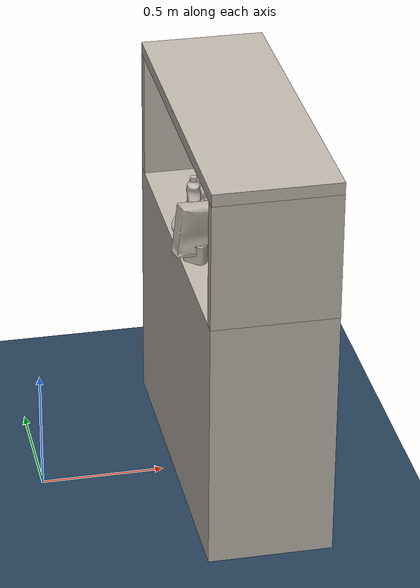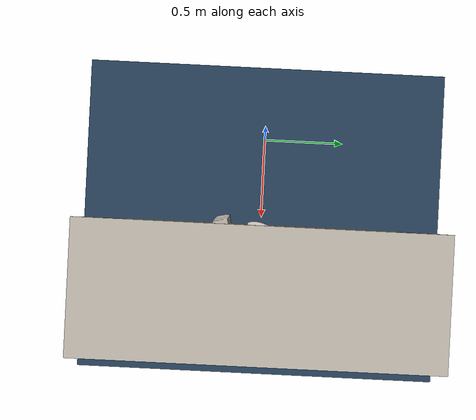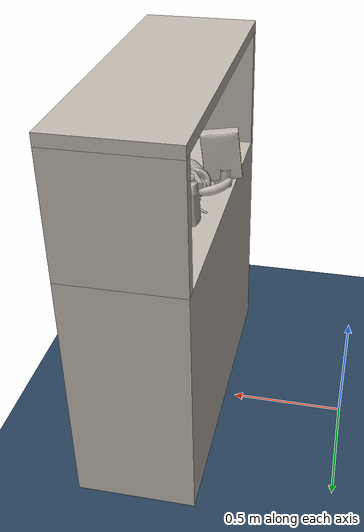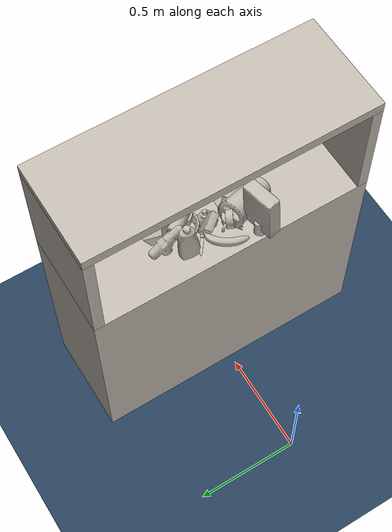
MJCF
<mujoco model="World">

  <compiler angle="radian" balanceinertia="true" inertiafromgeom="true" meshdir="/home/pracsys/GraspClutter6D_local" texturedir="/home/pracsys/GraspClutter6D_local" autolimits="true" />

  <option integrator="Euler" cone="elliptic" solver="CG" noslip_iterations="2">
    <flag warmstart="disable" multiccd="enable" />
  </option>

  <default>
    <geom density="10" />
  </default>

  <asset>

    <texture type="skybox" builtin="flat" rgb1="1 1 1" rgb2="0 0 0" width="512" height="512" />
    <texture name="grid" type="2d" builtin="checker" width="512" height="512" rgb1=".1 .2 .3" rgb2=".2 .3 .4" />
    <material name="grid" texture="grid" texrepeat="2 2" texuniform="true" specular="0" shininess="0" reflectance="0" emission="1" />

    <texture file="models/rs_table/ceramic.png" type="cube" name="tex-ceramic" />
    <material name="table_ceramic" reflectance="0.0" shininess="0.0" specular="0.2" texrepeat="1 1" texture="tex-ceramic" />
  <texture name="obj_000001_0_tex" type="2d" file="models_obj_m/obj_000001/obj_000001.png" /><material name="obj_000001_0_mat" texture="obj_000001_0_tex" specular="1.0" shininess="0.0" /><mesh name="obj_000001_0_vis" file="models_obj_m/obj_000001/obj_000001.obj" /><mesh name="obj_000001_0_obj_000001_collision_0" file="models_obj_m/obj_000001/obj_000001_collision_0.obj" /><mesh name="obj_000001_0_obj_000001_collision_1" file="models_obj_m/obj_000001/obj_000001_collision_1.obj" /><mesh name="obj_000001_0_obj_000001_collision_2" file="models_obj_m/obj_000001/obj_000001_collision_2.obj" /><mesh name="obj_000001_0_obj_000001_collision_3" file="models_obj_m/obj_000001/obj_000001_collision_3.obj" /><texture name="obj_000002_0_tex" type="2d" file="models_obj_m/obj_000002/obj_000002.png" /><material name="obj_000002_0_mat" texture="obj_000002_0_tex" specular="1.0" shininess="0.0" /><mesh name="obj_000002_0_vis" file="models_obj_m/obj_000002/obj_000002.obj" /><mesh name="obj_000002_0_obj_000002_collision_0" file="models_obj_m/obj_000002/obj_000002_collision_0.obj" /><mesh name="obj_000002_0_obj_000002_collision_1" file="models_obj_m/obj_000002/obj_000002_collision_1.obj" /><mesh name="obj_000002_0_obj_000002_collision_2" file="models_obj_m/obj_000002/obj_000002_collision_2.obj" /><mesh name="obj_000002_0_obj_000002_collision_3" file="models_obj_m/obj_000002/obj_000002_collision_3.obj" /><mesh name="obj_000002_0_obj_000002_collision_4" file="models_obj_m/obj_000002/obj_000002_collision_4.obj" /><mesh name="obj_000002_0_obj_000002_collision_5" file="models_obj_m/obj_000002/obj_000002_collision_5.obj" /><mesh name="obj_000002_0_obj_000002_collision_6" file="models_obj_m/obj_000002/obj_000002_collision_6.obj" /><mesh name="obj_000002_0_obj_000002_collision_7" file="models_obj_m/obj_000002/obj_000002_collision_7.obj" /><mesh name="obj_000002_0_obj_000002_collision_8" file="models_obj_m/obj_000002/obj_000002_collision_8.obj" /><mesh name="obj_000002_0_obj_000002_collision_9" file="models_obj_m/obj_000002/obj_000002_collision_9.obj" /><mesh name="obj_000002_0_obj_000002_collision_10" file="models_obj_m/obj_000002/obj_000002_collision_10.obj" /><mesh name="obj_000002_0_obj_000002_collision_11" file="models_obj_m/obj_000002/obj_000002_collision_11.obj" /><texture name="obj_000003_0_tex" type="2d" file="models_obj_m/obj_000003/obj_000003.png" /><material name="obj_000003_0_mat" texture="obj_000003_0_tex" specular="1.0" shininess="0.0" /><mesh name="obj_000003_0_vis" file="models_obj_m/obj_000003/obj_000003.obj" /><mesh name="obj_000003_0_obj_000003_collision_0" file="models_obj_m/obj_000003/obj_000003_collision_0.obj" /><mesh name="obj_000003_0_obj_000003_collision_1" file="models_obj_m/obj_000003/obj_000003_collision_1.obj" /><texture name="obj_000004_0_tex" type="2d" file="models_obj_m/obj_000004/obj_000004.png" /><material name="obj_000004_0_mat" texture="obj_000004_0_tex" specular="1.0" shininess="0.0" /><mesh name="obj_000004_0_vis" file="models_obj_m/obj_000004/obj_000004.obj" /><mesh name="obj_000004_0_obj_000004_collision_0" file="models_obj_m/obj_000004/obj_000004_collision_0.obj" /><mesh name="obj_000004_0_obj_000004_collision_1" file="models_obj_m/obj_000004/obj_000004_collision_1.obj" /><mesh name="obj_000004_0_obj_000004_collision_2" file="models_obj_m/obj_000004/obj_000004_collision_2.obj" /><mesh name="obj_000004_0_obj_000004_collision_3" file="models_obj_m/obj_000004/obj_000004_collision_3.obj" /><mesh name="obj_000004_0_obj_000004_collision_4" file="models_obj_m/obj_000004/obj_000004_collision_4.obj" /><mesh name="obj_000004_0_obj_000004_collision_5" file="models_obj_m/obj_000004/obj_000004_collision_5.obj" /><mesh name="obj_000004_0_obj_000004_collision_6" file="models_obj_m/obj_000004/obj_000004_collision_6.obj" /><mesh name="obj_000004_0_obj_000004_collision_7" file="models_obj_m/obj_000004/obj_000004_collision_7.obj" /><mesh name="obj_000004_0_obj_000004_collision_8" file="models_obj_m/obj_000004/obj_000004_collision_8.obj" /><mesh name="obj_000004_0_obj_000004_collision_9" file="models_obj_m/obj_000004/obj_000004_collision_9.obj" /><mesh name="obj_000004_0_obj_000004_collision_10" file="models_obj_m/obj_000004/obj_000004_collision_10.obj" /><mesh name="obj_000004_0_obj_000004_collision_11" file="models_obj_m/obj_000004/obj_000004_collision_11.obj" /><mesh name="obj_000004_0_obj_000004_collision_12" file="models_obj_m/obj_000004/obj_000004_collision_12.obj" /><mesh name="obj_000004_0_obj_000004_collision_13" file="models_obj_m/obj_000004/obj_000004_collision_13.obj" /><mesh name="obj_000004_0_obj_000004_collision_14" file="models_obj_m/obj_000004/obj_000004_collision_14.obj" /><mesh name="obj_000004_0_obj_000004_collision_15" file="models_obj_m/obj_000004/obj_000004_collision_15.obj" /><mesh name="obj_000004_0_obj_000004_collision_16" file="models_obj_m/obj_000004/obj_000004_collision_16.obj" /><mesh name="obj_000004_0_obj_000004_collision_17" file="models_obj_m/obj_000004/obj_000004_collision_17.obj" /><mesh name="obj_000004_0_obj_000004_collision_18" file="models_obj_m/obj_000004/obj_000004_collision_18.obj" /><mesh name="obj_000004_0_obj_000004_collision_19" file="models_obj_m/obj_000004/obj_000004_collision_19.obj" /><mesh name="obj_000004_0_obj_000004_collision_20" file="models_obj_m/obj_000004/obj_000004_collision_20.obj" /><mesh name="obj_000004_0_obj_000004_collision_21" file="models_obj_m/obj_000004/obj_000004_collision_21.obj" /><mesh name="obj_000004_0_obj_000004_collision_22" file="models_obj_m/obj_000004/obj_000004_collision_22.obj" /><texture name="obj_000005_0_tex" type="2d" file="models_obj_m/obj_000005/obj_000005.png" /><material name="obj_000005_0_mat" texture="obj_000005_0_tex" specular="1.0" shininess="0.0" /><mesh name="obj_000005_0_vis" file="models_obj_m/obj_000005/obj_000005.obj" /><mesh name="obj_000005_0_obj_000005_collision_0" file="models_obj_m/obj_000005/obj_000005_collision_0.obj" /><mesh name="obj_000005_0_obj_000005_collision_1" file="models_obj_m/obj_000005/obj_000005_collision_1.obj" /><mesh name="obj_000005_0_obj_000005_collision_2" file="models_obj_m/obj_000005/obj_000005_collision_2.obj" /><mesh name="obj_000005_0_obj_000005_collision_3" file="models_obj_m/obj_000005/obj_000005_collision_3.obj" /><texture name="obj_000006_0_tex" type="2d" file="models_obj_m/obj_000006/obj_000006.png" /><material name="obj_000006_0_mat" texture="obj_000006_0_tex" specular="1.0" shininess="0.0" /><mesh name="obj_000006_0_vis" file="models_obj_m/obj_000006/obj_000006.obj" /><mesh name="obj_000006_0_obj_000006_collision_0" file="models_obj_m/obj_000006/obj_000006_collision_0.obj" /><mesh name="obj_000006_0_obj_000006_collision_1" file="models_obj_m/obj_000006/obj_000006_collision_1.obj" /><mesh name="obj_000006_0_obj_000006_collision_2" file="models_obj_m/obj_000006/obj_000006_collision_2.obj" /><mesh name="obj_000006_0_obj_000006_collision_3" file="models_obj_m/obj_000006/obj_000006_collision_3.obj" /><mesh name="obj_000006_0_obj_000006_collision_4" file="models_obj_m/obj_000006/obj_000006_collision_4.obj" /><mesh name="obj_000006_0_obj_000006_collision_5" file="models_obj_m/obj_000006/obj_000006_collision_5.obj" /><mesh name="obj_000006_0_obj_000006_collision_6" file="models_obj_m/obj_000006/obj_000006_collision_6.obj" /><mesh name="obj_000006_0_obj_000006_collision_7" file="models_obj_m/obj_000006/obj_000006_collision_7.obj" /><mesh name="obj_000006_0_obj_000006_collision_8" file="models_obj_m/obj_000006/obj_000006_collision_8.obj" /><mesh name="obj_000006_0_obj_000006_collision_9" file="models_obj_m/obj_000006/obj_000006_collision_9.obj" /><mesh name="obj_000006_0_obj_000006_collision_10" file="models_obj_m/obj_000006/obj_000006_collision_10.obj" /><mesh name="obj_000006_0_obj_000006_collision_11" file="models_obj_m/obj_000006/obj_000006_collision_11.obj" /><mesh name="obj_000006_0_obj_000006_collision_12" file="models_obj_m/obj_000006/obj_000006_collision_12.obj" /><mesh name="obj_000006_0_obj_000006_collision_13" file="models_obj_m/obj_000006/obj_000006_collision_13.obj" /><texture name="obj_000007_0_tex" type="2d" file="models_obj_m/obj_000007/obj_000007.png" /><material name="obj_000007_0_mat" texture="obj_000007_0_tex" specular="1.0" shininess="0.0" /><mesh name="obj_000007_0_vis" file="models_obj_m/obj_000007/obj_000007.obj" /><mesh name="obj_000007_0_obj_000007_collision_0" file="models_obj_m/obj_000007/obj_000007_collision_0.obj" /><mesh name="obj_000007_0_obj_000007_collision_1" file="models_obj_m/obj_000007/obj_000007_collision_1.obj" /><mesh name="obj_000007_0_obj_000007_collision_2" file="models_obj_m/obj_000007/obj_000007_collision_2.obj" /><mesh name="obj_000007_0_obj_000007_collision_3" file="models_obj_m/obj_000007/obj_000007_collision_3.obj" /><mesh name="obj_000007_0_obj_000007_collision_4" file="models_obj_m/obj_000007/obj_000007_collision_4.obj" /><mesh name="obj_000007_0_obj_000007_collision_5" file="models_obj_m/obj_000007/obj_000007_collision_5.obj" /><mesh name="obj_000007_0_obj_000007_collision_6" file="models_obj_m/obj_000007/obj_000007_collision_6.obj" /><mesh name="obj_000007_0_obj_000007_collision_7" file="models_obj_m/obj_000007/obj_000007_collision_7.obj" /><mesh name="obj_000007_0_obj_000007_collision_8" file="models_obj_m/obj_000007/obj_000007_collision_8.obj" /><texture name="obj_000008_0_tex" type="2d" file="models_obj_m/obj_000008/obj_000008.png" /><material name="obj_000008_0_mat" texture="obj_000008_0_tex" specular="1.0" shininess="0.0" /><mesh name="obj_000008_0_vis" file="models_obj_m/obj_000008/obj_000008.obj" /><mesh name="obj_000008_0_obj_000008_collision_0" file="models_obj_m/obj_000008/obj_000008_collision_0.obj" /><mesh name="obj_000008_0_obj_000008_collision_1" file="models_obj_m/obj_000008/obj_000008_collision_1.obj" /><texture name="obj_000009_0_tex" type="2d" file="models_obj_m/obj_000009/obj_000010.png" /><material name="obj_000009_0_mat" texture="obj_000009_0_tex" specular="1.0" shininess="0.0" /><mesh name="obj_000009_0_vis" file="models_obj_m/obj_000009/obj_000009.obj" /><mesh name="obj_000009_0_obj_000009_collision_0" file="models_obj_m/obj_000009/obj_000009_collision_0.obj" /><mesh name="obj_000009_0_obj_000009_collision_1" file="models_obj_m/obj_000009/obj_000009_collision_1.obj" /><mesh name="obj_000009_0_obj_000009_collision_2" file="models_obj_m/obj_000009/obj_000009_collision_2.obj" /><mesh name="obj_000009_0_obj_000009_collision_3" file="models_obj_m/obj_000009/obj_000009_collision_3.obj" /><mesh name="obj_000009_0_obj_000009_collision_4" file="models_obj_m/obj_000009/obj_000009_collision_4.obj" /><mesh name="obj_000009_0_obj_000009_collision_5" file="models_obj_m/obj_000009/obj_000009_collision_5.obj" /><mesh name="obj_000009_0_obj_000009_collision_6" file="models_obj_m/obj_000009/obj_000009_collision_6.obj" /><mesh name="obj_000009_0_obj_000009_collision_7" file="models_obj_m/obj_000009/obj_000009_collision_7.obj" /><mesh name="obj_000009_0_obj_000009_collision_8" file="models_obj_m/obj_000009/obj_000009_collision_8.obj" /><mesh name="obj_000009_0_obj_000009_collision_9" file="models_obj_m/obj_000009/obj_000009_collision_9.obj" /><mesh name="obj_000009_0_obj_000009_collision_10" file="models_obj_m/obj_000009/obj_000009_collision_10.obj" /><mesh name="obj_000009_0_obj_000009_collision_11" file="models_obj_m/obj_000009/obj_000009_collision_11.obj" /><mesh name="obj_000009_0_obj_000009_collision_12" file="models_obj_m/obj_000009/obj_000009_collision_12.obj" /><mesh name="obj_000009_0_obj_000009_collision_13" file="models_obj_m/obj_000009/obj_000009_collision_13.obj" /><mesh name="obj_000009_0_obj_000009_collision_14" file="models_obj_m/obj_000009/obj_000009_collision_14.obj" /><mesh name="obj_000009_0_obj_000009_collision_15" file="models_obj_m/obj_000009/obj_000009_collision_15.obj" /><mesh name="obj_000009_0_obj_000009_collision_16" file="models_obj_m/obj_000009/obj_000009_collision_16.obj" /><mesh name="obj_000009_0_obj_000009_collision_17" file="models_obj_m/obj_000009/obj_000009_collision_17.obj" /><mesh name="obj_000009_0_obj_000009_collision_18" file="models_obj_m/obj_000009/obj_000009_collision_18.obj" /><mesh name="obj_000009_0_obj_000009_collision_19" file="models_obj_m/obj_000009/obj_000009_collision_19.obj" /><texture name="obj_000010_0_tex" type="2d" file="models_obj_m/obj_000010/obj_000011.png" /><material name="obj_000010_0_mat" texture="obj_000010_0_tex" specular="1.0" shininess="0.0" /><mesh name="obj_000010_0_vis" file="models_obj_m/obj_000010/obj_000010.obj" /><mesh name="obj_000010_0_obj_000010_collision_0" file="models_obj_m/obj_000010/obj_000010_collision_0.obj" /><mesh name="obj_000010_0_obj_000010_collision_1" file="models_obj_m/obj_000010/obj_000010_collision_1.obj" /><texture name="obj_000011_0_tex" type="2d" file="models_obj_m/obj_000011/obj_000011.png" /><material name="obj_000011_0_mat" texture="obj_000011_0_tex" specular="1.0" shininess="0.0" /><mesh name="obj_000011_0_vis" file="models_obj_m/obj_000011/obj_000011.obj" /><mesh name="obj_000011_0_obj_000011_collision_0" file="models_obj_m/obj_000011/obj_000011_collision_0.obj" /><mesh name="obj_000011_0_obj_000011_collision_1" file="models_obj_m/obj_000011/obj_000011_collision_1.obj" /><texture name="obj_000012_0_tex" type="2d" file="models_obj_m/obj_000012/obj_000013.png" /><material name="obj_000012_0_mat" texture="obj_000012_0_tex" specular="1.0" shininess="0.0" /><mesh name="obj_000012_0_vis" file="models_obj_m/obj_000012/obj_000012.obj" /><mesh name="obj_000012_0_obj_000012_collision_0" file="models_obj_m/obj_000012/obj_000012_collision_0.obj" /><mesh name="obj_000012_0_obj_000012_collision_1" file="models_obj_m/obj_000012/obj_000012_collision_1.obj" /><mesh name="obj_000012_0_obj_000012_collision_2" file="models_obj_m/obj_000012/obj_000012_collision_2.obj" /><texture name="obj_000013_0_tex" type="2d" file="models_obj_m/obj_000013/obj_000014.png" /><material name="obj_000013_0_mat" texture="obj_000013_0_tex" specular="1.0" shininess="0.0" /><mesh name="obj_000013_0_vis" file="models_obj_m/obj_000013/obj_000013.obj" /><mesh name="obj_000013_0_obj_000013_collision_0" file="models_obj_m/obj_000013/obj_000013_collision_0.obj" /><mesh name="obj_000013_0_obj_000013_collision_1" file="models_obj_m/obj_000013/obj_000013_collision_1.obj" /><mesh name="obj_000013_0_obj_000013_collision_2" file="models_obj_m/obj_000013/obj_000013_collision_2.obj" /><mesh name="obj_000013_0_obj_000013_collision_3" file="models_obj_m/obj_000013/obj_000013_collision_3.obj" /><mesh name="obj_000013_0_obj_000013_collision_4" file="models_obj_m/obj_000013/obj_000013_collision_4.obj" /><mesh name="obj_000013_0_obj_000013_collision_5" file="models_obj_m/obj_000013/obj_000013_collision_5.obj" /><mesh name="obj_000013_0_obj_000013_collision_6" file="models_obj_m/obj_000013/obj_000013_collision_6.obj" /><mesh name="obj_000013_0_obj_000013_collision_7" file="models_obj_m/obj_000013/obj_000013_collision_7.obj" /><mesh name="obj_000013_0_obj_000013_collision_8" file="models_obj_m/obj_000013/obj_000013_collision_8.obj" /><mesh name="obj_000013_0_obj_000013_collision_9" file="models_obj_m/obj_000013/obj_000013_collision_9.obj" /><mesh name="obj_000013_0_obj_000013_collision_10" file="models_obj_m/obj_000013/obj_000013_collision_10.obj" /><mesh name="obj_000013_0_obj_000013_collision_11" file="models_obj_m/obj_000013/obj_000013_collision_11.obj" /><mesh name="obj_000013_0_obj_000013_collision_12" file="models_obj_m/obj_000013/obj_000013_collision_12.obj" /><mesh name="obj_000013_0_obj_000013_collision_13" file="models_obj_m/obj_000013/obj_000013_collision_13.obj" /><mesh name="obj_000013_0_obj_000013_collision_14" file="models_obj_m/obj_000013/obj_000013_collision_14.obj" /><mesh name="obj_000013_0_obj_000013_collision_15" file="models_obj_m/obj_000013/obj_000013_collision_15.obj" /><mesh name="obj_000013_0_obj_000013_collision_16" file="models_obj_m/obj_000013/obj_000013_collision_16.obj" /><mesh name="obj_000013_0_obj_000013_collision_17" file="models_obj_m/obj_000013/obj_000013_collision_17.obj" /><mesh name="obj_000013_0_obj_000013_collision_18" file="models_obj_m/obj_000013/obj_000013_collision_18.obj" /><mesh name="obj_000013_0_obj_000013_collision_19" file="models_obj_m/obj_000013/obj_000013_collision_19.obj" /><mesh name="obj_000013_0_obj_000013_collision_20" file="models_obj_m/obj_000013/obj_000013_collision_20.obj" /><mesh name="obj_000013_0_obj_000013_collision_21" file="models_obj_m/obj_000013/obj_000013_collision_21.obj" /><mesh name="obj_000013_0_obj_000013_collision_22" file="models_obj_m/obj_000013/obj_000013_collision_22.obj" /><mesh name="obj_000013_0_obj_000013_collision_23" file="models_obj_m/obj_000013/obj_000013_collision_23.obj" /><mesh name="obj_000013_0_obj_000013_collision_24" file="models_obj_m/obj_000013/obj_000013_collision_24.obj" /><mesh name="obj_000013_0_obj_000013_collision_25" file="models_obj_m/obj_000013/obj_000013_collision_25.obj" /><mesh name="obj_000013_0_obj_000013_collision_26" file="models_obj_m/obj_000013/obj_000013_collision_26.obj" /><mesh name="obj_000013_0_obj_000013_collision_27" file="models_obj_m/obj_000013/obj_000013_collision_27.obj" /><mesh name="obj_000013_0_obj_000013_collision_28" file="models_obj_m/obj_000013/obj_000013_collision_28.obj" /><mesh name="obj_000013_0_obj_000013_collision_29" file="models_obj_m/obj_000013/obj_000013_collision_29.obj" /><mesh name="obj_000013_0_obj_000013_collision_30" file="models_obj_m/obj_000013/obj_000013_collision_30.obj" /><mesh name="obj_000013_0_obj_000013_collision_31" file="models_obj_m/obj_000013/obj_000013_collision_31.obj" /><mesh name="obj_000013_0_obj_000013_collision_32" file="models_obj_m/obj_000013/obj_000013_collision_32.obj" /><mesh name="obj_000013_0_obj_000013_collision_33" file="models_obj_m/obj_000013/obj_000013_collision_33.obj" /><mesh name="obj_000013_0_obj_000013_collision_34" file="models_obj_m/obj_000013/obj_000013_collision_34.obj" /><mesh name="obj_000013_0_obj_000013_collision_35" file="models_obj_m/obj_000013/obj_000013_collision_35.obj" /><mesh name="obj_000013_0_obj_000013_collision_36" file="models_obj_m/obj_000013/obj_000013_collision_36.obj" /><mesh name="obj_000013_0_obj_000013_collision_37" file="models_obj_m/obj_000013/obj_000013_collision_37.obj" /><mesh name="obj_000013_0_obj_000013_collision_38" file="models_obj_m/obj_000013/obj_000013_collision_38.obj" /><mesh name="obj_000013_0_obj_000013_collision_39" file="models_obj_m/obj_000013/obj_000013_collision_39.obj" /><mesh name="obj_000013_0_obj_000013_collision_40" file="models_obj_m/obj_000013/obj_000013_collision_40.obj" /><mesh name="obj_000013_0_obj_000013_collision_41" file="models_obj_m/obj_000013/obj_000013_collision_41.obj" /><mesh name="obj_000013_0_obj_000013_collision_42" file="models_obj_m/obj_000013/obj_000013_collision_42.obj" /><texture name="obj_000014_0_tex" type="2d" file="models_obj_m/obj_000014/obj_000014.png" /><material name="obj_000014_0_mat" texture="obj_000014_0_tex" specular="1.0" shininess="0.0" /><mesh name="obj_000014_0_vis" file="models_obj_m/obj_000014/obj_000014.obj" /><mesh name="obj_000014_0_obj_000014_collision_0" file="models_obj_m/obj_000014/obj_000014_collision_0.obj" /><mesh name="obj_000014_0_obj_000014_collision_1" file="models_obj_m/obj_000014/obj_000014_collision_1.obj" /><mesh name="obj_000014_0_obj_000014_collision_2" file="models_obj_m/obj_000014/obj_000014_collision_2.obj" /><mesh name="obj_000014_0_obj_000014_collision_3" file="models_obj_m/obj_000014/obj_000014_collision_3.obj" /><mesh name="obj_000014_0_obj_000014_collision_4" file="models_obj_m/obj_000014/obj_000014_collision_4.obj" /><mesh name="obj_000014_0_obj_000014_collision_5" file="models_obj_m/obj_000014/obj_000014_collision_5.obj" /><mesh name="obj_000014_0_obj_000014_collision_6" file="models_obj_m/obj_000014/obj_000014_collision_6.obj" /><mesh name="obj_000014_0_obj_000014_collision_7" file="models_obj_m/obj_000014/obj_000014_collision_7.obj" /><mesh name="obj_000014_0_obj_000014_collision_8" file="models_obj_m/obj_000014/obj_000014_collision_8.obj" /><mesh name="obj_000014_0_obj_000014_collision_9" file="models_obj_m/obj_000014/obj_000014_collision_9.obj" /><mesh name="obj_000014_0_obj_000014_collision_10" file="models_obj_m/obj_000014/obj_000014_collision_10.obj" /><mesh name="obj_000014_0_obj_000014_collision_11" file="models_obj_m/obj_000014/obj_000014_collision_11.obj" /><mesh name="obj_000014_0_obj_000014_collision_12" file="models_obj_m/obj_000014/obj_000014_collision_12.obj" /><mesh name="obj_000014_0_obj_000014_collision_13" file="models_obj_m/obj_000014/obj_000014_collision_13.obj" /><mesh name="obj_000014_0_obj_000014_collision_14" file="models_obj_m/obj_000014/obj_000014_collision_14.obj" /><mesh name="obj_000014_0_obj_000014_collision_15" file="models_obj_m/obj_000014/obj_000014_collision_15.obj" /><mesh name="obj_000014_0_obj_000014_collision_16" file="models_obj_m/obj_000014/obj_000014_collision_16.obj" /><mesh name="obj_000014_0_obj_000014_collision_17" file="models_obj_m/obj_000014/obj_000014_collision_17.obj" /><mesh name="obj_000014_0_obj_000014_collision_18" file="models_obj_m/obj_000014/obj_000014_collision_18.obj" /><mesh name="obj_000014_0_obj_000014_collision_19" file="models_obj_m/obj_000014/obj_000014_collision_19.obj" /><mesh name="obj_000014_0_obj_000014_collision_20" file="models_obj_m/obj_000014/obj_000014_collision_20.obj" /><mesh name="obj_000014_0_obj_000014_collision_21" file="models_obj_m/obj_000014/obj_000014_collision_21.obj" /><mesh name="obj_000014_0_obj_000014_collision_22" file="models_obj_m/obj_000014/obj_000014_collision_22.obj" /><mesh name="obj_000014_0_obj_000014_collision_23" file="models_obj_m/obj_000014/obj_000014_collision_23.obj" /><mesh name="obj_000014_0_obj_000014_collision_24" file="models_obj_m/obj_000014/obj_000014_collision_24.obj" /><mesh name="obj_000014_0_obj_000014_collision_25" file="models_obj_m/obj_000014/obj_000014_collision_25.obj" /><mesh name="obj_000014_0_obj_000014_collision_26" file="models_obj_m/obj_000014/obj_000014_collision_26.obj" /><mesh name="obj_000014_0_obj_000014_collision_27" file="models_obj_m/obj_000014/obj_000014_collision_27.obj" /><mesh name="obj_000014_0_obj_000014_collision_28" file="models_obj_m/obj_000014/obj_000014_collision_28.obj" /><mesh name="obj_000014_0_obj_000014_collision_29" file="models_obj_m/obj_000014/obj_000014_collision_29.obj" /><mesh name="obj_000014_0_obj_000014_collision_30" file="models_obj_m/obj_000014/obj_000014_collision_30.obj" /><mesh name="obj_000014_0_obj_000014_collision_31" file="models_obj_m/obj_000014/obj_000014_collision_31.obj" /><mesh name="obj_000014_0_obj_000014_collision_32" file="models_obj_m/obj_000014/obj_000014_collision_32.obj" /><mesh name="obj_000014_0_obj_000014_collision_33" file="models_obj_m/obj_000014/obj_000014_collision_33.obj" /><mesh name="obj_000014_0_obj_000014_collision_34" file="models_obj_m/obj_000014/obj_000014_collision_34.obj" /><mesh name="obj_000014_0_obj_000014_collision_35" file="models_obj_m/obj_000014/obj_000014_collision_35.obj" /><mesh name="obj_000014_0_obj_000014_collision_36" file="models_obj_m/obj_000014/obj_000014_collision_36.obj" /><mesh name="obj_000014_0_obj_000014_collision_37" file="models_obj_m/obj_000014/obj_000014_collision_37.obj" /><mesh name="obj_000014_0_obj_000014_collision_38" file="models_obj_m/obj_000014/obj_000014_collision_38.obj" /><texture name="obj_000015_0_tex" type="2d" file="models_obj_m/obj_000015/obj_000015.png" /><material name="obj_000015_0_mat" texture="obj_000015_0_tex" specular="1.0" shininess="0.0" /><mesh name="obj_000015_0_vis" file="models_obj_m/obj_000015/obj_000015.obj" /><mesh name="obj_000015_0_obj_000015_collision_0" file="models_obj_m/obj_000015/obj_000015_collision_0.obj" /><mesh name="obj_000015_0_obj_000015_collision_1" file="models_obj_m/obj_000015/obj_000015_collision_1.obj" /><texture name="obj_000016_0_tex" type="2d" file="models_obj_m/obj_000016/obj_000016.png" /><material name="obj_000016_0_mat" texture="obj_000016_0_tex" specular="1.0" shininess="0.0" /><mesh name="obj_000016_0_vis" file="models_obj_m/obj_000016/obj_000016.obj" /><mesh name="obj_000016_0_obj_000016_collision_0" file="models_obj_m/obj_000016/obj_000016_collision_0.obj" /><mesh name="obj_000016_0_obj_000016_collision_1" file="models_obj_m/obj_000016/obj_000016_collision_1.obj" /><texture name="obj_000017_0_tex" type="2d" file="models_obj_m/obj_000017/obj_000018.png" /><material name="obj_000017_0_mat" texture="obj_000017_0_tex" specular="1.0" shininess="0.0" /><mesh name="obj_000017_0_vis" file="models_obj_m/obj_000017/obj_000017.obj" /><mesh name="obj_000017_0_obj_000017_collision_0" file="models_obj_m/obj_000017/obj_000017_collision_0.obj" /><mesh name="obj_000017_0_obj_000017_collision_1" file="models_obj_m/obj_000017/obj_000017_collision_1.obj" /><mesh name="obj_000017_0_obj_000017_collision_2" file="models_obj_m/obj_000017/obj_000017_collision_2.obj" /><mesh name="obj_000017_0_obj_000017_collision_3" file="models_obj_m/obj_000017/obj_000017_collision_3.obj" /><mesh name="obj_000017_0_obj_000017_collision_4" file="models_obj_m/obj_000017/obj_000017_collision_4.obj" /><mesh name="obj_000017_0_obj_000017_collision_5" file="models_obj_m/obj_000017/obj_000017_collision_5.obj" /><mesh name="obj_000017_0_obj_000017_collision_6" file="models_obj_m/obj_000017/obj_000017_collision_6.obj" /><mesh name="obj_000017_0_obj_000017_collision_7" file="models_obj_m/obj_000017/obj_000017_collision_7.obj" /><mesh name="obj_000017_0_obj_000017_collision_8" file="models_obj_m/obj_000017/obj_000017_collision_8.obj" /><mesh name="obj_000017_0_obj_000017_collision_9" file="models_obj_m/obj_000017/obj_000017_collision_9.obj" /><mesh name="obj_000017_0_obj_000017_collision_10" file="models_obj_m/obj_000017/obj_000017_collision_10.obj" /><mesh name="obj_000017_0_obj_000017_collision_11" file="models_obj_m/obj_000017/obj_000017_collision_11.obj" /><mesh name="obj_000017_0_obj_000017_collision_12" file="models_obj_m/obj_000017/obj_000017_collision_12.obj" /><mesh name="obj_000017_0_obj_000017_collision_13" file="models_obj_m/obj_000017/obj_000017_collision_13.obj" /><mesh name="obj_000017_0_obj_000017_collision_14" file="models_obj_m/obj_000017/obj_000017_collision_14.obj" /><mesh name="obj_000017_0_obj_000017_collision_15" file="models_obj_m/obj_000017/obj_000017_collision_15.obj" /><mesh name="obj_000017_0_obj_000017_collision_16" file="models_obj_m/obj_000017/obj_000017_collision_16.obj" /><mesh name="obj_000017_0_obj_000017_collision_17" file="models_obj_m/obj_000017/obj_000017_collision_17.obj" /><mesh name="obj_000017_0_obj_000017_collision_18" file="models_obj_m/obj_000017/obj_000017_collision_18.obj" /><mesh name="obj_000017_0_obj_000017_collision_19" file="models_obj_m/obj_000017/obj_000017_collision_19.obj" /><mesh name="obj_000017_0_obj_000017_collision_20" file="models_obj_m/obj_000017/obj_000017_collision_20.obj" /><mesh name="obj_000017_0_obj_000017_collision_21" file="models_obj_m/obj_000017/obj_000017_collision_21.obj" /><mesh name="obj_000017_0_obj_000017_collision_22" file="models_obj_m/obj_000017/obj_000017_collision_22.obj" /><mesh name="obj_000017_0_obj_000017_collision_23" file="models_obj_m/obj_000017/obj_000017_collision_23.obj" /><mesh name="obj_000017_0_obj_000017_collision_24" file="models_obj_m/obj_000017/obj_000017_collision_24.obj" /><mesh name="obj_000017_0_obj_000017_collision_25" file="models_obj_m/obj_000017/obj_000017_collision_25.obj" /><mesh name="obj_000017_0_obj_000017_collision_26" file="models_obj_m/obj_000017/obj_000017_collision_26.obj" /><mesh name="obj_000017_0_obj_000017_collision_27" file="models_obj_m/obj_000017/obj_000017_collision_27.obj" /></asset>

  <worldbody>
    <geom name="floor" size="2 2 0.05" type="plane" material="grid" condim="3" />
    <light directional="true" pos="-0.5 0.5 3" dir="0 0 -1" castshadow="false" diffuse="1 1 1" />
    <body name="workspace" pos="0.8 0 0">
      <geom name="shelf_bottom" size="0.25 0.68 0.525" pos="0 0 0.525" type="box" material="table_ceramic" />
      <geom name="shelf_top" size="0.25 0.68 0.025" pos="0 0 1.595" type="box" material="table_ceramic" />
      <geom name="shelf_padding_left" size="0.25 0.025 0.26" pos="0 -0.655 1.31" type="box" material="table_ceramic" />
      <geom name="shelf_padding_right" size="0.25 0.025 0.26" pos="0 0.655 1.31" type="box" material="table_ceramic" />
      <geom name="shelf_padding_back" size="0.05 0.63 0.26" pos="0.2 0 1.31" type="box" material="table_ceramic" />
    </body>
  <body name="obj_000001_0" pos="0.8041671678662738 0.11459093323557962 1.0458136459146916" quat="0.2059333407587482 -0.006246730700879997 0.0006055885666920169 -0.9785458961039997"><joint name="obj_000001_0_joint" type="free" limited="false" actuatorfrclimited="false" /><geom name="obj_000001_0_geom" type="mesh" contype="0" conaffinity="0" group="1" mesh="obj_000001_0_vis" material="obj_000001_0_mat" /><geom type="mesh" contype="3" conaffinity="3" group="3" rgba="0.9088700260871841 0.5571276366315294 0.02905709149002622 1" mesh="obj_000001_0_obj_000001_collision_0" /><geom type="mesh" contype="3" conaffinity="3" group="3" rgba="0.6410593324381463 0.8402607000713928 0.7776918396385317 1" mesh="obj_000001_0_obj_000001_collision_1" /><geom type="mesh" contype="3" conaffinity="3" group="3" rgba="0.7741652165627951 0.3179101861807435 0.21643336209038533 1" mesh="obj_000001_0_obj_000001_collision_2" /><geom type="mesh" contype="3" conaffinity="3" group="3" rgba="0.8899250795032356 0.5115007140285017 0.5329157655053317 1" mesh="obj_000001_0_obj_000001_collision_3" /></body><body name="obj_000002_0" pos="0.6044538971987572 -0.16174184113051873 1.1995195778031622" quat="0.03979770663144523 0.7645480532681519 -0.6422321593536755 -0.03768647347089031"><joint name="obj_000002_0_joint" type="free" limited="false" actuatorfrclimited="false" /><geom name="obj_000002_0_geom" type="mesh" contype="0" conaffinity="0" group="1" mesh="obj_000002_0_vis" material="obj_000002_0_mat" /><geom type="mesh" contype="3" conaffinity="3" group="3" rgba="0.9306362109825914 0.8330381231198574 0.5807939113573184 1" mesh="obj_000002_0_obj_000002_collision_0" /><geom type="mesh" contype="3" conaffinity="3" group="3" rgba="0.22912688553814242 0.3875596124141527 0.6327362632726903 1" mesh="obj_000002_0_obj_000002_collision_1" /><geom type="mesh" contype="3" conaffinity="3" group="3" rgba="0.5626259340568875 0.06667345172874573 0.9646088448813395 1" mesh="obj_000002_0_obj_000002_collision_2" /><geom type="mesh" contype="3" conaffinity="3" group="3" rgba="0.2846097720774853 0.35893411128232966 0.5389009556396629 1" mesh="obj_000002_0_obj_000002_collision_3" /><geom type="mesh" contype="3" conaffinity="3" group="3" rgba="0.4508218349405261 0.28618698217910077 0.07910182632008134 1" mesh="obj_000002_0_obj_000002_collision_4" /><geom type="mesh" contype="3" conaffinity="3" group="3" rgba="0.9884794335745274 0.515469558330875 0.0707067722442899 1" mesh="obj_000002_0_obj_000002_collision_5" /><geom type="mesh" contype="3" conaffinity="3" group="3" rgba="0.498884402525659 0.4938823346017336 0.12591961447178301 1" mesh="obj_000002_0_obj_000002_collision_6" /><geom type="mesh" contype="3" conaffinity="3" group="3" rgba="0.1950625664278297 0.8240004663666761 0.4881804849656727 1" mesh="obj_000002_0_obj_000002_collision_7" /><geom type="mesh" contype="3" conaffinity="3" group="3" rgba="0.3132936482834743 0.5610004182168095 0.20088818676924047 1" mesh="obj_000002_0_obj_000002_collision_8" /><geom type="mesh" contype="3" conaffinity="3" group="3" rgba="0.13324297406595753 0.30489124850385396 0.8325815622552574 1" mesh="obj_000002_0_obj_000002_collision_9" /><geom type="mesh" contype="3" conaffinity="3" group="3" rgba="0.33502585031452325 0.012724563165045999 0.5652884737523166 1" mesh="obj_000002_0_obj_000002_collision_10" /><geom type="mesh" contype="3" conaffinity="3" group="3" rgba="0.7875683506774841 0.0948782425132162 0.929563921752164 1" mesh="obj_000002_0_obj_000002_collision_11" /></body><body name="obj_000003_0" pos="0.7771623761262496 -0.11544738625142567 1.0567397266112755" quat="0.6635911521299045 0.22625245523749885 -0.44665495405778377 0.5558380711408212"><joint name="obj_000003_0_joint" type="free" limited="false" actuatorfrclimited="false" /><geom name="obj_000003_0_geom" type="mesh" contype="0" conaffinity="0" group="1" mesh="obj_000003_0_vis" material="obj_000003_0_mat" /><geom type="mesh" contype="3" conaffinity="3" group="3" rgba="0.522509730671621 0.2757706064801614 0.3354227120316712 1" mesh="obj_000003_0_obj_000003_collision_0" /><geom type="mesh" contype="3" conaffinity="3" group="3" rgba="0.5516880957351997 0.30786775055087157 0.8022185455408283 1" mesh="obj_000003_0_obj_000003_collision_1" /></body><body name="obj_000004_0" pos="0.7585391839905387 0.15245712396869743 1.1488513146682184" quat="0.27049172279302025 0.5508227038603807 -0.3507581110595931 0.7073876761283798"><joint name="obj_000004_0_joint" type="free" limited="false" actuatorfrclimited="false" /><geom name="obj_000004_0_geom" type="mesh" contype="0" conaffinity="0" group="1" mesh="obj_000004_0_vis" material="obj_000004_0_mat" /><geom type="mesh" contype="3" conaffinity="3" group="3" rgba="0.9006364109388675 0.519839966144869 0.14706711888770962 1" mesh="obj_000004_0_obj_000004_collision_0" /><geom type="mesh" contype="3" conaffinity="3" group="3" rgba="0.5381862094377646 0.9079565306792778 0.5860391296454226 1" mesh="obj_000004_0_obj_000004_collision_1" /><geom type="mesh" contype="3" conaffinity="3" group="3" rgba="0.5480980169898275 0.08959733837327 0.9583058214694634 1" mesh="obj_000004_0_obj_000004_collision_2" /><geom type="mesh" contype="3" conaffinity="3" group="3" rgba="0.7348365413245799 0.9954340839881138 0.10043620261647124 1" mesh="obj_000004_0_obj_000004_collision_3" /><geom type="mesh" contype="3" conaffinity="3" group="3" rgba="0.15354151346682998 0.3992493537144245 0.9018485612644948 1" mesh="obj_000004_0_obj_000004_collision_4" /><geom type="mesh" contype="3" conaffinity="3" group="3" rgba="0.5002296823323479 0.06984196192688352 0.14791196849948396 1" mesh="obj_000004_0_obj_000004_collision_5" /><geom type="mesh" contype="3" conaffinity="3" group="3" rgba="0.8801698595600871 0.26981609947861984 0.5413749209604201 1" mesh="obj_000004_0_obj_000004_collision_6" /><geom type="mesh" contype="3" conaffinity="3" group="3" rgba="0.7455497002678284 0.842184542639177 0.5322202076862146 1" mesh="obj_000004_0_obj_000004_collision_7" /><geom type="mesh" contype="3" conaffinity="3" group="3" rgba="0.4442591382610347 0.03638499919506211 0.32497635780499234 1" mesh="obj_000004_0_obj_000004_collision_8" /><geom type="mesh" contype="3" conaffinity="3" group="3" rgba="0.347627915730894 0.06862688241171433 0.2798410387094733 1" mesh="obj_000004_0_obj_000004_collision_9" /><geom type="mesh" contype="3" conaffinity="3" group="3" rgba="0.37436058860529653 0.8129023073913533 0.26614439644261234 1" mesh="obj_000004_0_obj_000004_collision_10" /><geom type="mesh" contype="3" conaffinity="3" group="3" rgba="0.6651690258226822 0.3522546747219869 0.10346100033130279 1" mesh="obj_000004_0_obj_000004_collision_11" /><geom type="mesh" contype="3" conaffinity="3" group="3" rgba="0.37709868933847024 0.90775268626264 0.22612048573823684 1" mesh="obj_000004_0_obj_000004_collision_12" /><geom type="mesh" contype="3" conaffinity="3" group="3" rgba="0.40627473735328157 0.5372136836683266 0.09197578627779501 1" mesh="obj_000004_0_obj_000004_collision_13" /><geom type="mesh" contype="3" conaffinity="3" group="3" rgba="0.5166762315831523 0.5043939028531624 0.5872248864695762 1" mesh="obj_000004_0_obj_000004_collision_14" /><geom type="mesh" contype="3" conaffinity="3" group="3" rgba="0.9082988442703623 0.180499146533042 0.06796330417599283 1" mesh="obj_000004_0_obj_000004_collision_15" /><geom type="mesh" contype="3" conaffinity="3" group="3" rgba="0.3943402105248509 0.6197627239371787 0.4344456177319421 1" mesh="obj_000004_0_obj_000004_collision_16" /><geom type="mesh" contype="3" conaffinity="3" group="3" rgba="0.7831743542292524 0.42593724102287467 0.6857518540249657 1" mesh="obj_000004_0_obj_000004_collision_17" /><geom type="mesh" contype="3" conaffinity="3" group="3" rgba="0.16096816650240264 0.6010361248517645 0.059463136740677824 1" mesh="obj_000004_0_obj_000004_collision_18" /><geom type="mesh" contype="3" conaffinity="3" group="3" rgba="0.44263326221518995 0.2502881781833013 0.38014160116271456 1" mesh="obj_000004_0_obj_000004_collision_19" /><geom type="mesh" contype="3" conaffinity="3" group="3" rgba="0.5463028526085283 0.845330838869169 0.028012824828687388 1" mesh="obj_000004_0_obj_000004_collision_20" /><geom type="mesh" contype="3" conaffinity="3" group="3" rgba="0.19910255883632533 0.853207251405083 0.4267815842990055 1" mesh="obj_000004_0_obj_000004_collision_21" /><geom type="mesh" contype="3" conaffinity="3" group="3" rgba="0.013081679159259063 0.8478266493247634 0.5767717804295942 1" mesh="obj_000004_0_obj_000004_collision_22" /></body><body name="obj_000005_0" pos="0.7369400869648297 0.0239024413621991 1.0646190460173999" quat="0.6981684744370854 -0.015602555488451122 0.06330613587010148 0.712958396209498"><joint name="obj_000005_0_joint" type="free" limited="false" actuatorfrclimited="false" /><geom name="obj_000005_0_geom" type="mesh" contype="0" conaffinity="0" group="1" mesh="obj_000005_0_vis" material="obj_000005_0_mat" /><geom type="mesh" contype="3" conaffinity="3" group="3" rgba="0.7022177830689367 0.5826341853352067 0.8165841864018348 1" mesh="obj_000005_0_obj_000005_collision_0" /><geom type="mesh" contype="3" conaffinity="3" group="3" rgba="0.8850110305129232 0.6858243586259702 0.23668113982222616 1" mesh="obj_000005_0_obj_000005_collision_1" /><geom type="mesh" contype="3" conaffinity="3" group="3" rgba="0.3521162735319521 0.8507480837221914 0.47569448758993216 1" mesh="obj_000005_0_obj_000005_collision_2" /><geom type="mesh" contype="3" conaffinity="3" group="3" rgba="0.9128805975392907 0.1623848974121762 0.6573614293432378 1" mesh="obj_000005_0_obj_000005_collision_3" /></body><body name="obj_000006_0" pos="0.6865298686922476 -0.05952314359515892 1.0896424206497959" quat="0.45248375962013476 -0.7243441821031738 -0.21531633036182596 -0.4735217323553692"><joint name="obj_000006_0_joint" type="free" limited="false" actuatorfrclimited="false" /><geom name="obj_000006_0_geom" type="mesh" contype="0" conaffinity="0" group="1" mesh="obj_000006_0_vis" material="obj_000006_0_mat" /><geom type="mesh" contype="3" conaffinity="3" group="3" rgba="0.2826735963389645 0.3732613789385052 0.7850961502526286 1" mesh="obj_000006_0_obj_000006_collision_0" /><geom type="mesh" contype="3" conaffinity="3" group="3" rgba="0.2778119464286495 0.852700815001951 0.9131251478975895 1" mesh="obj_000006_0_obj_000006_collision_1" /><geom type="mesh" contype="3" conaffinity="3" group="3" rgba="0.8020587813288036 0.3025792521954269 0.26202108232011456 1" mesh="obj_000006_0_obj_000006_collision_2" /><geom type="mesh" contype="3" conaffinity="3" group="3" rgba="0.8749284451958235 0.7193776905239141 0.13458988549502138 1" mesh="obj_000006_0_obj_000006_collision_3" /><geom type="mesh" contype="3" conaffinity="3" group="3" rgba="0.2130188599738736 0.6558868892940936 0.9509039115354172 1" mesh="obj_000006_0_obj_000006_collision_4" /><geom type="mesh" contype="3" conaffinity="3" group="3" rgba="0.7150440817211193 0.6337582813459244 0.5959789356841197 1" mesh="obj_000006_0_obj_000006_collision_5" /><geom type="mesh" contype="3" conaffinity="3" group="3" rgba="0.5914430060148156 0.6397733981720453 0.4770481905761884 1" mesh="obj_000006_0_obj_000006_collision_6" /><geom type="mesh" contype="3" conaffinity="3" group="3" rgba="0.5370695134833949 0.5650036394015392 0.4193565416983073 1" mesh="obj_000006_0_obj_000006_collision_7" /><geom type="mesh" contype="3" conaffinity="3" group="3" rgba="0.45822516380627654 0.5322962868917284 0.22216684784693663 1" mesh="obj_000006_0_obj_000006_collision_8" /><geom type="mesh" contype="3" conaffinity="3" group="3" rgba="0.006992755819853924 0.22617836990136309 0.6404316243166618 1" mesh="obj_000006_0_obj_000006_collision_9" /><geom type="mesh" contype="3" conaffinity="3" group="3" rgba="0.11371882398649225 0.6403057750389807 0.6565213489306491 1" mesh="obj_000006_0_obj_000006_collision_10" /><geom type="mesh" contype="3" conaffinity="3" group="3" rgba="0.5479453169554588 0.8715696065342489 0.8827485230284868 1" mesh="obj_000006_0_obj_000006_collision_11" /><geom type="mesh" contype="3" conaffinity="3" group="3" rgba="0.29639456023491106 0.716942263751537 0.6685544064500213 1" mesh="obj_000006_0_obj_000006_collision_12" /><geom type="mesh" contype="3" conaffinity="3" group="3" rgba="0.24060769408938665 0.11426077536513679 0.6643453630239089 1" mesh="obj_000006_0_obj_000006_collision_13" /></body><body name="obj_000007_0" pos="0.6918755656058568 0.04418252690666222 1.139107377921116" quat="0.007933237594695402 0.3875612920518077 0.3873905685817558 0.8364579224433847"><joint name="obj_000007_0_joint" type="free" limited="false" actuatorfrclimited="false" /><geom name="obj_000007_0_geom" type="mesh" contype="0" conaffinity="0" group="1" mesh="obj_000007_0_vis" material="obj_000007_0_mat" /><geom type="mesh" contype="3" conaffinity="3" group="3" rgba="0.8352706854217573 0.9362994234831694 0.293846875833475 1" mesh="obj_000007_0_obj_000007_collision_0" /><geom type="mesh" contype="3" conaffinity="3" group="3" rgba="0.19905331661291714 0.4589533019713804 0.06900329109829795 1" mesh="obj_000007_0_obj_000007_collision_1" /><geom type="mesh" contype="3" conaffinity="3" group="3" rgba="0.09308414112438301 0.15050338013169284 0.9151604575537959 1" mesh="obj_000007_0_obj_000007_collision_2" /><geom type="mesh" contype="3" conaffinity="3" group="3" rgba="0.5321495441159548 0.7015834228771671 0.15224241133161276 1" mesh="obj_000007_0_obj_000007_collision_3" /><geom type="mesh" contype="3" conaffinity="3" group="3" rgba="0.23157390654164967 0.05668202494056429 0.16362068486781922 1" mesh="obj_000007_0_obj_000007_collision_4" /><geom type="mesh" contype="3" conaffinity="3" group="3" rgba="0.434682609159569 0.02891498183785912 0.4135716003922958 1" mesh="obj_000007_0_obj_000007_collision_5" /><geom type="mesh" contype="3" conaffinity="3" group="3" rgba="0.3986174188827881 0.6060589903191558 0.6080009673791554 1" mesh="obj_000007_0_obj_000007_collision_6" /><geom type="mesh" contype="3" conaffinity="3" group="3" rgba="0.19756852407433856 0.9438271125215391 0.3383181352472745 1" mesh="obj_000007_0_obj_000007_collision_7" /><geom type="mesh" contype="3" conaffinity="3" group="3" rgba="0.8336516710698538 0.1310754047491739 0.3201867808203366 1" mesh="obj_000007_0_obj_000007_collision_8" /></body><body name="obj_000008_0" pos="0.7702872276258868 0.07678803598468772 1.0567739916868906" quat="0.6383009919556707 0.09232526164155318 0.0803097209934498 0.7599988410814715"><joint name="obj_000008_0_joint" type="free" limited="false" actuatorfrclimited="false" /><geom name="obj_000008_0_geom" type="mesh" contype="0" conaffinity="0" group="1" mesh="obj_000008_0_vis" material="obj_000008_0_mat" /><geom type="mesh" contype="3" conaffinity="3" group="3" rgba="0.01671885427652786 0.8783564729505184 0.3287082962157769 1" mesh="obj_000008_0_obj_000008_collision_0" /><geom type="mesh" contype="3" conaffinity="3" group="3" rgba="0.2759906839891276 0.5799351894391934 0.46463070880456725 1" mesh="obj_000008_0_obj_000008_collision_1" /></body><body name="obj_000009_0" pos="0.6005743756671917 -0.16173061430279512 1.1015719307774354" quat="0.9162361276314821 0.017041831134574456 0.0049311798807142315 -0.400245696890586"><joint name="obj_000009_0_joint" type="free" limited="false" actuatorfrclimited="false" /><geom name="obj_000009_0_geom" type="mesh" contype="0" conaffinity="0" group="1" mesh="obj_000009_0_vis" material="obj_000009_0_mat" /><geom type="mesh" contype="3" conaffinity="3" group="3" rgba="0.4701424646800718 0.15058678152224558 0.03232555140522908 1" mesh="obj_000009_0_obj_000009_collision_0" /><geom type="mesh" contype="3" conaffinity="3" group="3" rgba="0.6334264391293729 0.7000588704139452 0.9101191958261439 1" mesh="obj_000009_0_obj_000009_collision_1" /><geom type="mesh" contype="3" conaffinity="3" group="3" rgba="0.4796571013469104 0.35150290582234567 0.6375226777586448 1" mesh="obj_000009_0_obj_000009_collision_2" /><geom type="mesh" contype="3" conaffinity="3" group="3" rgba="0.8005895298046106 0.9629796370374781 0.317100801488033 1" mesh="obj_000009_0_obj_000009_collision_3" /><geom type="mesh" contype="3" conaffinity="3" group="3" rgba="0.7316817429575484 0.8125950918942385 0.9770420869852225 1" mesh="obj_000009_0_obj_000009_collision_4" /><geom type="mesh" contype="3" conaffinity="3" group="3" rgba="0.027540659115147248 0.9471989066929749 0.9744029211039258 1" mesh="obj_000009_0_obj_000009_collision_5" /><geom type="mesh" contype="3" conaffinity="3" group="3" rgba="0.2468027165587915 0.11355498828593935 0.640482643727051 1" mesh="obj_000009_0_obj_000009_collision_6" /><geom type="mesh" contype="3" conaffinity="3" group="3" rgba="0.26381115444349046 0.5064233410291425 0.06434432684247016 1" mesh="obj_000009_0_obj_000009_collision_7" /><geom type="mesh" contype="3" conaffinity="3" group="3" rgba="0.39104113124687934 0.2576147934487044 0.9823472559836796 1" mesh="obj_000009_0_obj_000009_collision_8" /><geom type="mesh" contype="3" conaffinity="3" group="3" rgba="0.9013360285468692 0.8336454994592718 0.7736518361085535 1" mesh="obj_000009_0_obj_000009_collision_9" /><geom type="mesh" contype="3" conaffinity="3" group="3" rgba="0.5638034510545271 0.2309865979911192 0.056178319664080933 1" mesh="obj_000009_0_obj_000009_collision_10" /><geom type="mesh" contype="3" conaffinity="3" group="3" rgba="0.07539982230460429 0.8840212053523439 0.37940438346802385 1" mesh="obj_000009_0_obj_000009_collision_11" /><geom type="mesh" contype="3" conaffinity="3" group="3" rgba="0.12997684997558534 0.2197119572502484 0.7348773851044048 1" mesh="obj_000009_0_obj_000009_collision_12" /><geom type="mesh" contype="3" conaffinity="3" group="3" rgba="0.4102032814193337 0.31374038786638225 0.9229380645994204 1" mesh="obj_000009_0_obj_000009_collision_13" /><geom type="mesh" contype="3" conaffinity="3" group="3" rgba="0.6775180913271598 0.3730860518815964 0.7560922645576079 1" mesh="obj_000009_0_obj_000009_collision_14" /><geom type="mesh" contype="3" conaffinity="3" group="3" rgba="0.20013413652544576 0.046709010626810876 0.4530831720844085 1" mesh="obj_000009_0_obj_000009_collision_15" /><geom type="mesh" contype="3" conaffinity="3" group="3" rgba="0.997743233778264 0.8720065066436486 0.22893873285390964 1" mesh="obj_000009_0_obj_000009_collision_16" /><geom type="mesh" contype="3" conaffinity="3" group="3" rgba="0.2486444461791405 0.8482398554397806 0.9913239367051718 1" mesh="obj_000009_0_obj_000009_collision_17" /><geom type="mesh" contype="3" conaffinity="3" group="3" rgba="0.8552881572534362 0.878526833870521 0.5714311973878448 1" mesh="obj_000009_0_obj_000009_collision_18" /><geom type="mesh" contype="3" conaffinity="3" group="3" rgba="0.6375258423342278 0.3334964947472784 0.042644175833863374 1" mesh="obj_000009_0_obj_000009_collision_19" /></body><body name="obj_000010_0" pos="0.5994390004327927 0.01364429931359512 1.1441539179693956" quat="0.98954130159142 0.0044340073210690665 -0.019066603747249666 -0.14291541780151062"><joint name="obj_000010_0_joint" type="free" limited="false" actuatorfrclimited="false" /><geom name="obj_000010_0_geom" type="mesh" contype="0" conaffinity="0" group="1" mesh="obj_000010_0_vis" material="obj_000010_0_mat" /><geom type="mesh" contype="3" conaffinity="3" group="3" rgba="0.8732881017396182 0.3343353395712876 0.08871879557869766 1" mesh="obj_000010_0_obj_000010_collision_0" /><geom type="mesh" contype="3" conaffinity="3" group="3" rgba="0.7768969898522989 0.17302799154634285 0.5980561258489338 1" mesh="obj_000010_0_obj_000010_collision_1" /></body><body name="obj_000011_0" pos="0.7257226712801113 -0.17043367090762093 1.0677269435345014" quat="0.42973176781234435 -0.4988421265894244 0.37273612423842883 0.6538768402079496"><joint name="obj_000011_0_joint" type="free" limited="false" actuatorfrclimited="false" /><geom name="obj_000011_0_geom" type="mesh" contype="0" conaffinity="0" group="1" mesh="obj_000011_0_vis" material="obj_000011_0_mat" /><geom type="mesh" contype="3" conaffinity="3" group="3" rgba="0.30507868086283874 0.9701993068122707 0.0021639835779936334 1" mesh="obj_000011_0_obj_000011_collision_0" /><geom type="mesh" contype="3" conaffinity="3" group="3" rgba="0.30046086308937203 0.33184924156596896 0.2382777103232726 1" mesh="obj_000011_0_obj_000011_collision_1" /></body><body name="obj_000012_0" pos="0.6606701080243629 0.15704775014827205 1.1297312480480906" quat="0.7165450720643127 -0.00735430959392795 0.006963541715786281 0.6974672629719031"><joint name="obj_000012_0_joint" type="free" limited="false" actuatorfrclimited="false" /><geom name="obj_000012_0_geom" type="mesh" contype="0" conaffinity="0" group="1" mesh="obj_000012_0_vis" material="obj_000012_0_mat" /><geom type="mesh" contype="3" conaffinity="3" group="3" rgba="0.7554614099521485 0.6486382034608017 0.7176584907668884 1" mesh="obj_000012_0_obj_000012_collision_0" /><geom type="mesh" contype="3" conaffinity="3" group="3" rgba="0.7007292636586778 0.4517934483878622 0.09276525431541405 1" mesh="obj_000012_0_obj_000012_collision_1" /><geom type="mesh" contype="3" conaffinity="3" group="3" rgba="0.20665389244215027 0.9686490753588884 0.0818582005279912 1" mesh="obj_000012_0_obj_000012_collision_2" /></body><body name="obj_000013_0" pos="0.7669399426153516 0.13796097082966383 1.0829731959326696" quat="0.914744502306963 0.003825718696073008 0.018836001758589682 -0.40357535159297786"><joint name="obj_000013_0_joint" type="free" limited="false" actuatorfrclimited="false" /><geom name="obj_000013_0_geom" type="mesh" contype="0" conaffinity="0" group="1" mesh="obj_000013_0_vis" material="obj_000013_0_mat" /><geom type="mesh" contype="3" conaffinity="3" group="3" rgba="0.7144449078304332 0.20729995565427417 0.9178363700574447 1" mesh="obj_000013_0_obj_000013_collision_0" /><geom type="mesh" contype="3" conaffinity="3" group="3" rgba="0.8679721083209072 0.681676504550008 0.39306036015103996 1" mesh="obj_000013_0_obj_000013_collision_1" /><geom type="mesh" contype="3" conaffinity="3" group="3" rgba="0.4222762318266222 0.7236405457523389 0.5776720096370943 1" mesh="obj_000013_0_obj_000013_collision_2" /><geom type="mesh" contype="3" conaffinity="3" group="3" rgba="0.3811132546629832 0.20215465648724362 0.7520145076915546 1" mesh="obj_000013_0_obj_000013_collision_3" /><geom type="mesh" contype="3" conaffinity="3" group="3" rgba="0.8942398171755435 0.15581696020393487 0.2948183730971583 1" mesh="obj_000013_0_obj_000013_collision_4" /><geom type="mesh" contype="3" conaffinity="3" group="3" rgba="0.2417240360311006 0.7592152106015807 0.3902675366012601 1" mesh="obj_000013_0_obj_000013_collision_5" /><geom type="mesh" contype="3" conaffinity="3" group="3" rgba="0.7575682610228988 0.71336761782297 0.9000744888221621 1" mesh="obj_000013_0_obj_000013_collision_6" /><geom type="mesh" contype="3" conaffinity="3" group="3" rgba="0.6446126328225535 0.791897169193733 0.903810115591806 1" mesh="obj_000013_0_obj_000013_collision_7" /><geom type="mesh" contype="3" conaffinity="3" group="3" rgba="0.16065949094204024 0.7129315196731527 0.26362017540303107 1" mesh="obj_000013_0_obj_000013_collision_8" /><geom type="mesh" contype="3" conaffinity="3" group="3" rgba="0.3807771090070753 0.2466972699876384 0.03935990556652813 1" mesh="obj_000013_0_obj_000013_collision_9" /><geom type="mesh" contype="3" conaffinity="3" group="3" rgba="0.13563712303681397 0.6930968980104955 0.5192151078476201 1" mesh="obj_000013_0_obj_000013_collision_10" /><geom type="mesh" contype="3" conaffinity="3" group="3" rgba="0.024566780316822356 0.28274751850143287 0.43892641421651424 1" mesh="obj_000013_0_obj_000013_collision_11" /><geom type="mesh" contype="3" conaffinity="3" group="3" rgba="0.9611355436206976 0.1398983653776168 0.013281849357456355 1" mesh="obj_000013_0_obj_000013_collision_12" /><geom type="mesh" contype="3" conaffinity="3" group="3" rgba="0.16394261226899853 0.18011486841153612 0.261500747000427 1" mesh="obj_000013_0_obj_000013_collision_13" /><geom type="mesh" contype="3" conaffinity="3" group="3" rgba="0.9372545164731062 0.43083457597005825 0.2977176404473417 1" mesh="obj_000013_0_obj_000013_collision_14" /><geom type="mesh" contype="3" conaffinity="3" group="3" rgba="0.031516698743391136 0.3219220373951125 0.8781862881808276 1" mesh="obj_000013_0_obj_000013_collision_15" /><geom type="mesh" contype="3" conaffinity="3" group="3" rgba="0.02675922996645186 0.9922976068282781 0.007381407445995691 1" mesh="obj_000013_0_obj_000013_collision_16" /><geom type="mesh" contype="3" conaffinity="3" group="3" rgba="0.2616329704439392 0.8542187029589711 0.7241329221218575 1" mesh="obj_000013_0_obj_000013_collision_17" /><geom type="mesh" contype="3" conaffinity="3" group="3" rgba="0.4206173565556577 0.19568760805702212 0.07953404942627174 1" mesh="obj_000013_0_obj_000013_collision_18" /><geom type="mesh" contype="3" conaffinity="3" group="3" rgba="0.6258372434102025 0.941102970428584 0.9848429359171544 1" mesh="obj_000013_0_obj_000013_collision_19" /><geom type="mesh" contype="3" conaffinity="3" group="3" rgba="0.48476862781453456 0.6464837012010779 0.09451531120989676 1" mesh="obj_000013_0_obj_000013_collision_20" /><geom type="mesh" contype="3" conaffinity="3" group="3" rgba="0.1499291510091808 0.6953859819117357 0.6465605447898165 1" mesh="obj_000013_0_obj_000013_collision_21" /><geom type="mesh" contype="3" conaffinity="3" group="3" rgba="0.10867033303428852 0.978104636023048 0.357697068924551 1" mesh="obj_000013_0_obj_000013_collision_22" /><geom type="mesh" contype="3" conaffinity="3" group="3" rgba="0.5296024898295869 0.79373291584904 0.9945877669564267 1" mesh="obj_000013_0_obj_000013_collision_23" /><geom type="mesh" contype="3" conaffinity="3" group="3" rgba="0.2535176902922558 0.7850034645037743 0.5109712695625952 1" mesh="obj_000013_0_obj_000013_collision_24" /><geom type="mesh" contype="3" conaffinity="3" group="3" rgba="0.6056982213796875 0.40921073467235836 0.09899078122809213 1" mesh="obj_000013_0_obj_000013_collision_25" /><geom type="mesh" contype="3" conaffinity="3" group="3" rgba="0.883355825637934 0.22180977392998258 0.02657703610970763 1" mesh="obj_000013_0_obj_000013_collision_26" /><geom type="mesh" contype="3" conaffinity="3" group="3" rgba="0.40558726586937655 0.4789794972792186 0.3060234025628258 1" mesh="obj_000013_0_obj_000013_collision_27" /><geom type="mesh" contype="3" conaffinity="3" group="3" rgba="0.40694994851305444 0.05141490066920784 0.738857658183313 1" mesh="obj_000013_0_obj_000013_collision_28" /><geom type="mesh" contype="3" conaffinity="3" group="3" rgba="0.08167123731304904 0.44468972618504576 0.909513688034694 1" mesh="obj_000013_0_obj_000013_collision_29" /><geom type="mesh" contype="3" conaffinity="3" group="3" rgba="0.43983320336223675 0.023288947525740622 0.31535110360234764 1" mesh="obj_000013_0_obj_000013_collision_30" /><geom type="mesh" contype="3" conaffinity="3" group="3" rgba="0.9246187387738158 0.19662054774999016 0.0025641556684291578 1" mesh="obj_000013_0_obj_000013_collision_31" /><geom type="mesh" contype="3" conaffinity="3" group="3" rgba="0.045116612411272294 0.03568353398017865 0.4988035813233547 1" mesh="obj_000013_0_obj_000013_collision_32" /><geom type="mesh" contype="3" conaffinity="3" group="3" rgba="0.9319052096815352 0.9810101582709009 0.3479210478200858 1" mesh="obj_000013_0_obj_000013_collision_33" /><geom type="mesh" contype="3" conaffinity="3" group="3" rgba="0.6159303212672878 0.5133135910288431 0.325090192866053 1" mesh="obj_000013_0_obj_000013_collision_34" /><geom type="mesh" contype="3" conaffinity="3" group="3" rgba="0.9849344998388689 0.24294440606249046 0.6152785687052574 1" mesh="obj_000013_0_obj_000013_collision_35" /><geom type="mesh" contype="3" conaffinity="3" group="3" rgba="0.23831369728617768 0.30135001589082866 0.01950178993412488 1" mesh="obj_000013_0_obj_000013_collision_36" /><geom type="mesh" contype="3" conaffinity="3" group="3" rgba="0.8893176464217286 0.9125313127217429 0.9492610344899751 1" mesh="obj_000013_0_obj_000013_collision_37" /><geom type="mesh" contype="3" conaffinity="3" group="3" rgba="0.051120110890551906 0.8122331757110894 0.932558326795465 1" mesh="obj_000013_0_obj_000013_collision_38" /><geom type="mesh" contype="3" conaffinity="3" group="3" rgba="0.5797100002940134 0.6688424793390167 0.625986013027617 1" mesh="obj_000013_0_obj_000013_collision_39" /><geom type="mesh" contype="3" conaffinity="3" group="3" rgba="0.8702933956914729 0.6777120300180547 0.8117268026780544 1" mesh="obj_000013_0_obj_000013_collision_40" /><geom type="mesh" contype="3" conaffinity="3" group="3" rgba="0.7113154344650927 0.4504182301539761 0.9850233708858935 1" mesh="obj_000013_0_obj_000013_collision_41" /><geom type="mesh" contype="3" conaffinity="3" group="3" rgba="0.6463048132580995 0.23232105267837944 0.9412536874981714 1" mesh="obj_000013_0_obj_000013_collision_42" /></body><body name="obj_000014_0" pos="0.6941073893964809 -0.06234296753415178 1.0474541053878095" quat="0.0029661742327397314 -0.546077670141015 -0.8374503174700904 0.02161818107582587"><joint name="obj_000014_0_joint" type="free" limited="false" actuatorfrclimited="false" /><geom name="obj_000014_0_geom" type="mesh" contype="0" conaffinity="0" group="1" mesh="obj_000014_0_vis" material="obj_000014_0_mat" /><geom type="mesh" contype="3" conaffinity="3" group="3" rgba="0.16141368952927726 0.8941132712421812 0.5548749728589505 1" mesh="obj_000014_0_obj_000014_collision_0" /><geom type="mesh" contype="3" conaffinity="3" group="3" rgba="0.8498791440201986 0.5078067392722992 0.18104551223069276 1" mesh="obj_000014_0_obj_000014_collision_1" /><geom type="mesh" contype="3" conaffinity="3" group="3" rgba="0.8943954905161718 0.3968195555274622 0.7506667206413482 1" mesh="obj_000014_0_obj_000014_collision_2" /><geom type="mesh" contype="3" conaffinity="3" group="3" rgba="0.35285466454019054 0.3172969522275877 0.7777097891043925 1" mesh="obj_000014_0_obj_000014_collision_3" /><geom type="mesh" contype="3" conaffinity="3" group="3" rgba="0.6717797492805505 0.27468490709077875 0.17325073818140246 1" mesh="obj_000014_0_obj_000014_collision_4" /><geom type="mesh" contype="3" conaffinity="3" group="3" rgba="0.7947496542642261 0.5505795486049172 0.24523806449691898 1" mesh="obj_000014_0_obj_000014_collision_5" /><geom type="mesh" contype="3" conaffinity="3" group="3" rgba="0.055183469003469154 0.8741690348288653 0.6355782986914638 1" mesh="obj_000014_0_obj_000014_collision_6" /><geom type="mesh" contype="3" conaffinity="3" group="3" rgba="0.13714783929055574 0.9099011487118126 0.046849323318082 1" mesh="obj_000014_0_obj_000014_collision_7" /><geom type="mesh" contype="3" conaffinity="3" group="3" rgba="0.5757321500485043 0.7653495890173662 0.11729263428082792 1" mesh="obj_000014_0_obj_000014_collision_8" /><geom type="mesh" contype="3" conaffinity="3" group="3" rgba="0.04262441774970249 0.20853658483044857 0.1703428205193146 1" mesh="obj_000014_0_obj_000014_collision_9" /><geom type="mesh" contype="3" conaffinity="3" group="3" rgba="0.7540479077019692 0.3915149318812796 0.4429325687742387 1" mesh="obj_000014_0_obj_000014_collision_10" /><geom type="mesh" contype="3" conaffinity="3" group="3" rgba="0.9209908675974051 0.10818362438838003 0.6189688407757469 1" mesh="obj_000014_0_obj_000014_collision_11" /><geom type="mesh" contype="3" conaffinity="3" group="3" rgba="0.8239539038983041 0.963565432161378 0.07680378701257484 1" mesh="obj_000014_0_obj_000014_collision_12" /><geom type="mesh" contype="3" conaffinity="3" group="3" rgba="0.3580527646207692 0.9396191389477992 0.6726680134980254 1" mesh="obj_000014_0_obj_000014_collision_13" /><geom type="mesh" contype="3" conaffinity="3" group="3" rgba="0.3187862019948787 0.842895426167915 0.30383779731684313 1" mesh="obj_000014_0_obj_000014_collision_14" /><geom type="mesh" contype="3" conaffinity="3" group="3" rgba="0.8290415048504837 0.43261520532805775 0.4960423319651849 1" mesh="obj_000014_0_obj_000014_collision_15" /><geom type="mesh" contype="3" conaffinity="3" group="3" rgba="0.47137951977516845 0.7080669244219827 0.5190940947326312 1" mesh="obj_000014_0_obj_000014_collision_16" /><geom type="mesh" contype="3" conaffinity="3" group="3" rgba="0.7270019138804638 0.08558543806348451 0.28134693023649016 1" mesh="obj_000014_0_obj_000014_collision_17" /><geom type="mesh" contype="3" conaffinity="3" group="3" rgba="0.2278750701799056 0.45829465031892036 0.24631126738678388 1" mesh="obj_000014_0_obj_000014_collision_18" /><geom type="mesh" contype="3" conaffinity="3" group="3" rgba="0.8345805016638979 0.20150630993040652 0.5303175522053208 1" mesh="obj_000014_0_obj_000014_collision_19" /><geom type="mesh" contype="3" conaffinity="3" group="3" rgba="0.21449831849224799 0.8815788784779822 0.4946040642073185 1" mesh="obj_000014_0_obj_000014_collision_20" /><geom type="mesh" contype="3" conaffinity="3" group="3" rgba="0.5201983270088316 0.07293896462298644 0.47589207267863676 1" mesh="obj_000014_0_obj_000014_collision_21" /><geom type="mesh" contype="3" conaffinity="3" group="3" rgba="0.6790069105260244 0.05281035932712075 0.8960063801553154 1" mesh="obj_000014_0_obj_000014_collision_22" /><geom type="mesh" contype="3" conaffinity="3" group="3" rgba="0.24152118753827823 0.6713577531353322 0.8759765939813601 1" mesh="obj_000014_0_obj_000014_collision_23" /><geom type="mesh" contype="3" conaffinity="3" group="3" rgba="0.8959852812192273 0.6685148885345674 0.043270461595834475 1" mesh="obj_000014_0_obj_000014_collision_24" /><geom type="mesh" contype="3" conaffinity="3" group="3" rgba="0.9103547626218504 0.037810082392731204 0.32968077117363426 1" mesh="obj_000014_0_obj_000014_collision_25" /><geom type="mesh" contype="3" conaffinity="3" group="3" rgba="0.8924690475590995 0.7858539504025231 0.5314529871560677 1" mesh="obj_000014_0_obj_000014_collision_26" /><geom type="mesh" contype="3" conaffinity="3" group="3" rgba="0.8776507752074951 0.006905611208717133 0.13662201660191675 1" mesh="obj_000014_0_obj_000014_collision_27" /><geom type="mesh" contype="3" conaffinity="3" group="3" rgba="0.8980953270074162 0.5018244752305326 0.015371112777743057 1" mesh="obj_000014_0_obj_000014_collision_28" /><geom type="mesh" contype="3" conaffinity="3" group="3" rgba="0.881652186049792 0.6680883818245129 0.8030035683379387 1" mesh="obj_000014_0_obj_000014_collision_29" /><geom type="mesh" contype="3" conaffinity="3" group="3" rgba="0.9161220339223549 0.8259454248436557 0.32114550413575527 1" mesh="obj_000014_0_obj_000014_collision_30" /><geom type="mesh" contype="3" conaffinity="3" group="3" rgba="0.6740594633112692 0.8978357800705399 0.7541896723125306 1" mesh="obj_000014_0_obj_000014_collision_31" /><geom type="mesh" contype="3" conaffinity="3" group="3" rgba="0.0727347622521074 0.5269632119735216 0.3031843793551897 1" mesh="obj_000014_0_obj_000014_collision_32" /><geom type="mesh" contype="3" conaffinity="3" group="3" rgba="0.42563563790720826 0.5797993794734493 0.5845484997962103 1" mesh="obj_000014_0_obj_000014_collision_33" /><geom type="mesh" contype="3" conaffinity="3" group="3" rgba="0.19592235314761497 0.4231444707325488 0.890859832481569 1" mesh="obj_000014_0_obj_000014_collision_34" /><geom type="mesh" contype="3" conaffinity="3" group="3" rgba="0.9949348150733605 0.608647559429353 0.15322985524005972 1" mesh="obj_000014_0_obj_000014_collision_35" /><geom type="mesh" contype="3" conaffinity="3" group="3" rgba="0.7858454240895385 0.323178255755149 0.9736177117477949 1" mesh="obj_000014_0_obj_000014_collision_36" /><geom type="mesh" contype="3" conaffinity="3" group="3" rgba="0.6648284999313376 0.9703306050755396 0.4425452240435842 1" mesh="obj_000014_0_obj_000014_collision_37" /><geom type="mesh" contype="3" conaffinity="3" group="3" rgba="0.8400435277741224 0.6937273949571666 0.6362434619528645 1" mesh="obj_000014_0_obj_000014_collision_38" /></body><body name="obj_000015_0" pos="0.7132514355931987 0.2103436219342818 1.0808857286930076" quat="0.6017229235727788 0.3458771056409929 0.6053914585441399 0.38961485208117536"><joint name="obj_000015_0_joint" type="free" limited="false" actuatorfrclimited="false" /><geom name="obj_000015_0_geom" type="mesh" contype="0" conaffinity="0" group="1" mesh="obj_000015_0_vis" material="obj_000015_0_mat" /><geom type="mesh" contype="3" conaffinity="3" group="3" rgba="0.3190316346741193 0.1952698898252364 0.8681956882216872 1" mesh="obj_000015_0_obj_000015_collision_0" /><geom type="mesh" contype="3" conaffinity="3" group="3" rgba="0.05496090459096381 0.16901046389765384 0.29761740439272677 1" mesh="obj_000015_0_obj_000015_collision_1" /></body><body name="obj_000016_0" pos="0.7919867238440546 0.2213709101666368 1.0566642368768602" quat="0.7604094307232258 -0.1745617877266854 0.1391721369909068 0.6098662117368258"><joint name="obj_000016_0_joint" type="free" limited="false" actuatorfrclimited="false" /><geom name="obj_000016_0_geom" type="mesh" contype="0" conaffinity="0" group="1" mesh="obj_000016_0_vis" material="obj_000016_0_mat" /><geom type="mesh" contype="3" conaffinity="3" group="3" rgba="0.26001420709121326 0.2392394811811206 0.8526178870500972 1" mesh="obj_000016_0_obj_000016_collision_0" /><geom type="mesh" contype="3" conaffinity="3" group="3" rgba="0.7022628207821711 0.8409075002048506 0.5809282073216406 1" mesh="obj_000016_0_obj_000016_collision_1" /></body><body name="obj_000017_0" pos="0.682302479856415 0.060794443133489307 1.0756682232411579" quat="0.8191989831503758 0.017247429885834734 -0.005986960969307176 0.5732187265486667"><joint name="obj_000017_0_joint" type="free" limited="false" actuatorfrclimited="false" /><geom name="obj_000017_0_geom" type="mesh" contype="0" conaffinity="0" group="1" mesh="obj_000017_0_vis" material="obj_000017_0_mat" /><geom type="mesh" contype="3" conaffinity="3" group="3" rgba="0.8300607436027256 0.7746450626520026 0.028259677595148802 1" mesh="obj_000017_0_obj_000017_collision_0" /><geom type="mesh" contype="3" conaffinity="3" group="3" rgba="0.8722382693318378 0.7274771061770118 0.3531693377771803 1" mesh="obj_000017_0_obj_000017_collision_1" /><geom type="mesh" contype="3" conaffinity="3" group="3" rgba="0.5980877609329729 0.08964925108942157 0.9827409328247976 1" mesh="obj_000017_0_obj_000017_collision_2" /><geom type="mesh" contype="3" conaffinity="3" group="3" rgba="0.12896852327670105 0.23262496541784183 0.708307388236716 1" mesh="obj_000017_0_obj_000017_collision_3" /><geom type="mesh" contype="3" conaffinity="3" group="3" rgba="0.49139690091838406 0.8926335265499304 0.5725586181467778 1" mesh="obj_000017_0_obj_000017_collision_4" /><geom type="mesh" contype="3" conaffinity="3" group="3" rgba="0.7937783832204612 0.42217433502668733 0.08859246894572148 1" mesh="obj_000017_0_obj_000017_collision_5" /><geom type="mesh" contype="3" conaffinity="3" group="3" rgba="0.31968501261458615 0.055692886468857505 0.13372686667046396 1" mesh="obj_000017_0_obj_000017_collision_6" /><geom type="mesh" contype="3" conaffinity="3" group="3" rgba="0.13222025522357372 0.17526274312101753 0.06896550916264677 1" mesh="obj_000017_0_obj_000017_collision_7" /><geom type="mesh" contype="3" conaffinity="3" group="3" rgba="0.619764861047721 0.6525147311748656 0.1945147804146634 1" mesh="obj_000017_0_obj_000017_collision_8" /><geom type="mesh" contype="3" conaffinity="3" group="3" rgba="0.7542938162430041 0.5932445765901436 0.7103646795954568 1" mesh="obj_000017_0_obj_000017_collision_9" /><geom type="mesh" contype="3" conaffinity="3" group="3" rgba="0.2524389464191312 0.4250197643184034 0.5484201401942239 1" mesh="obj_000017_0_obj_000017_collision_10" /><geom type="mesh" contype="3" conaffinity="3" group="3" rgba="0.12747630615148275 0.8773457669467531 0.2903516195529615 1" mesh="obj_000017_0_obj_000017_collision_11" /><geom type="mesh" contype="3" conaffinity="3" group="3" rgba="0.36705284536176563 0.43857882856348707 0.1921920616144135 1" mesh="obj_000017_0_obj_000017_collision_12" /><geom type="mesh" contype="3" conaffinity="3" group="3" rgba="0.020558595977965055 0.21526825750714773 0.772725517547242 1" mesh="obj_000017_0_obj_000017_collision_13" /><geom type="mesh" contype="3" conaffinity="3" group="3" rgba="0.10547210479742064 0.9890552387987501 0.2674120461420154 1" mesh="obj_000017_0_obj_000017_collision_14" /><geom type="mesh" contype="3" conaffinity="3" group="3" rgba="0.5360270978662599 0.047077211229519134 0.4732059459915734 1" mesh="obj_000017_0_obj_000017_collision_15" /><geom type="mesh" contype="3" conaffinity="3" group="3" rgba="0.32224738434780165 0.15368027561517583 0.33294464645257393 1" mesh="obj_000017_0_obj_000017_collision_16" /><geom type="mesh" contype="3" conaffinity="3" group="3" rgba="0.062153350878422775 0.15503522074777376 0.031107839074490995 1" mesh="obj_000017_0_obj_000017_collision_17" /><geom type="mesh" contype="3" conaffinity="3" group="3" rgba="0.8894341143153127 0.9274654291220618 0.8960713779272304 1" mesh="obj_000017_0_obj_000017_collision_18" /><geom type="mesh" contype="3" conaffinity="3" group="3" rgba="0.6407302652172892 0.7024854384405839 0.8132487939275371 1" mesh="obj_000017_0_obj_000017_collision_19" /><geom type="mesh" contype="3" conaffinity="3" group="3" rgba="0.4219128475173737 0.12864992232644612 0.6362594297911104 1" mesh="obj_000017_0_obj_000017_collision_20" /><geom type="mesh" contype="3" conaffinity="3" group="3" rgba="0.6553489886066428 0.7743604048132783 0.24056368137361295 1" mesh="obj_000017_0_obj_000017_collision_21" /><geom type="mesh" contype="3" conaffinity="3" group="3" rgba="0.0020229106216186343 0.307330070733969 0.17780994515928916 1" mesh="obj_000017_0_obj_000017_collision_22" /><geom type="mesh" contype="3" conaffinity="3" group="3" rgba="0.6179802568288576 0.3727782053738845 0.7596080060713355 1" mesh="obj_000017_0_obj_000017_collision_23" /><geom type="mesh" contype="3" conaffinity="3" group="3" rgba="0.2543795317816884 0.44576637101255845 0.39514403782482055 1" mesh="obj_000017_0_obj_000017_collision_24" /><geom type="mesh" contype="3" conaffinity="3" group="3" rgba="0.1432102771351177 0.4024857781955712 0.7572092015391542 1" mesh="obj_000017_0_obj_000017_collision_25" /><geom type="mesh" contype="3" conaffinity="3" group="3" rgba="0.5090090981373664 0.38439090770599904 0.5322095653024554 1" mesh="obj_000017_0_obj_000017_collision_26" /><geom type="mesh" contype="3" conaffinity="3" group="3" rgba="0.40226807840950896 0.5364817416307209 0.6608784606481888 1" mesh="obj_000017_0_obj_000017_collision_27" /></body></worldbody>

<size memory="64M" /></mujoco>
